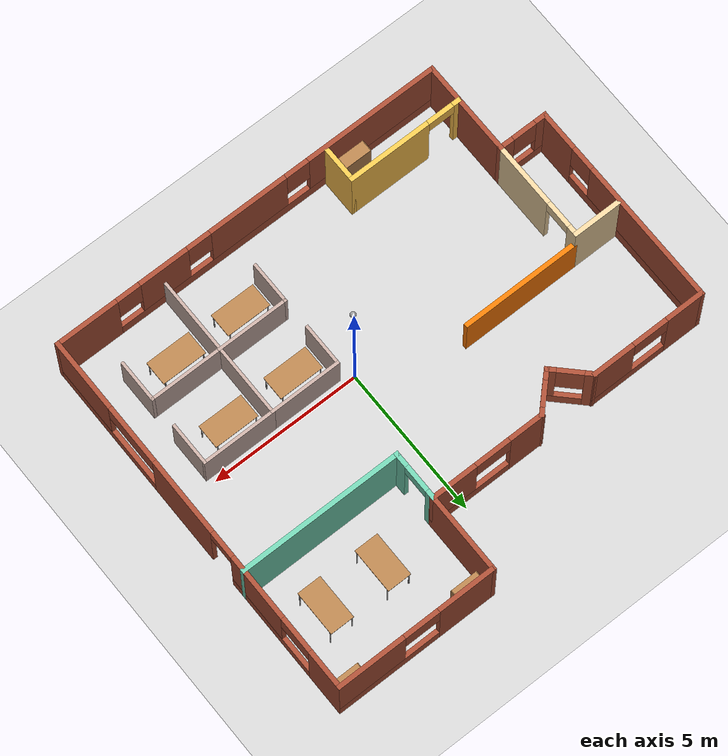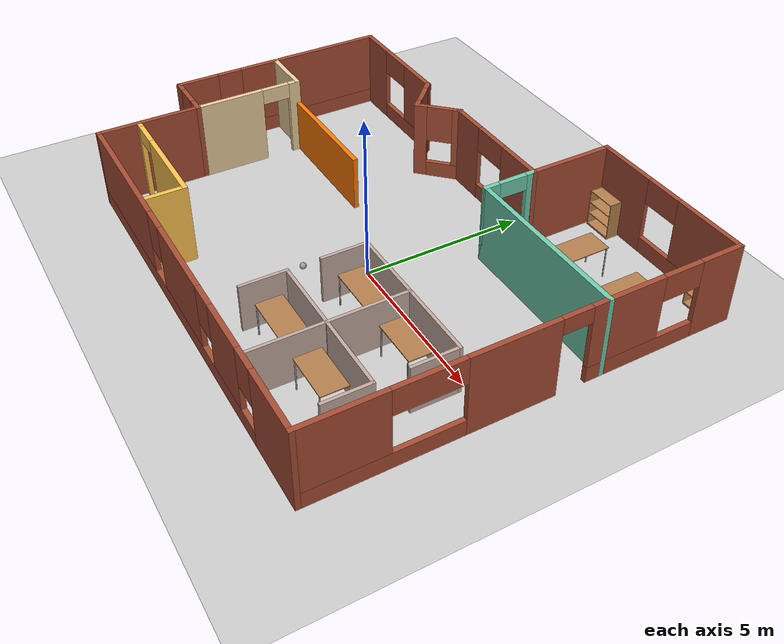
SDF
<sdf version="1.6">
 <world name="default">
  <plugin name="helloworld" filename="libhello.so"/>
  <light name="sun" type="directional">
   <pose>0 0 10 0 -0 0</pose>
   <diffuse>0.8 0.8 0.8 1</diffuse>
   <specular>0.2 0.2 0.2 1</specular>
   <attenuation>
    <range>1000</range>
    <constant>0.9</constant>
    <linear>0.01</linear>
    <quadratic>0.001</quadratic>
   </attenuation>
   <direction>-0.5 0.1 -0.9</direction>
  </light>
  <model name="ground_plane">
   <static>1</static>
   <link name="link">
    <collision name="collision">
     <geometry><plane><normal>0 0 1</normal><size>100 100</size></plane></geometry>
     <surface><friction><ode><mu>100</mu><mu2>50</mu2></ode></friction></surface>
    </collision>
    <visual name="visual">
     <cast_shadows>0</cast_shadows>
     <geometry><plane><normal>0 0 1</normal><size>100 100</size></plane></geometry>
     <material>
      <script><uri>file://media/materials/scripts/gazebo.material</uri><name>Gazebo/Grey</name></script>
     </material>
    </visual>
   </link>
  </model>
  <gravity>0 0 -9.8</gravity>
  <magnetic_field>6e-06 2.3e-05 -4.2e-05</magnetic_field>
  <atmosphere type="adiabatic"/>
  <physics name="default_physics" default="0" type="ode">
   <max_step_size>0.001</max_step_size>
   <real_time_factor>1</real_time_factor>
   <real_time_update_rate>1000</real_time_update_rate>
  </physics>
  <scene><ambient>0.4 0.4 0.4 1</ambient><background>0.7 0.7 0.7 1</background><shadows>1</shadows></scene>
  <spherical_coordinates>
   <surface_model>EARTH_WGS84</surface_model>
   <latitude_deg>0</latitude_deg>
   <longitude_deg>0</longitude_deg>
   <elevation>0</elevation>
   <heading_deg>0</heading_deg>
  </spherical_coordinates>
  <model name="MyOfficeWorld">
   <pose>-1.09735 1.08179 0 0 -0 0</pose>
   <link name="Wall_33">
    <pose>-7.47671 0.275 0 0 -0 1.5708</pose>
    <visual name="Wall_33_Visual_0">
     <pose>-2.83689 0 1.25 0 -0 0</pose>
     <geometry><box><size>1.32622 0.15 2.5</size></box></geometry>
     <material>
      <script><uri>file://media/materials/scripts/gazebo.material</uri><name>Gazebo/Bricks</name></script>
      <ambient>1 1 1 1</ambient>
     </material>
     <meta><layer>0</layer></meta>
    </visual>
    <collision name="Wall_33_Collision_0">
     <geometry><box><size>1.32622 0.15 2.5</size></box></geometry>
     <pose>-2.83689 0 1.25 0 -0 0</pose>
    </collision>
    <visual name="Wall_33_Visual_1">
     <pose>0.66311 0 0.25 0 -0 0</pose>
     <geometry><box><size>5.67378 0.15 0.5</size></box></geometry>
     <material>
      <script><uri>file://media/materials/scripts/gazebo.material</uri><name>Gazebo/Bricks</name></script>
      <ambient>1 1 1 1</ambient>
     </material>
     <meta><layer>0</layer></meta>
    </visual>
    <collision name="Wall_33_Collision_1">
     <geometry><box><size>5.67378 0.15 0.5</size></box></geometry>
     <pose>0.66311 0 0.25 0 -0 0</pose>
    </collision>
    <visual name="Wall_33_Visual_2">
     <pose>1.06311 0 1.5 0 -0 0</pose>
     <geometry><box><size>4.87378 0.15 2</size></box></geometry>
     <material>
      <script><uri>file://media/materials/scripts/gazebo.material</uri><name>Gazebo/Bricks</name></script>
      <ambient>1 1 1 1</ambient>
     </material>
     <meta><layer>0</layer></meta>
    </visual>
    <collision name="Wall_33_Collision_2">
     <geometry><box><size>4.87378 0.15 2</size></box></geometry>
     <pose>1.06311 0 1.5 0 -0 0</pose>
    </collision>
    <visual name="Wall_33_Visual_3">
     <pose>-1.77378 0 1.9 0 -0 0</pose>
     <geometry><box><size>0.8 0.15 1.2</size></box></geometry>
     <material>
      <script><uri>file://media/materials/scripts/gazebo.material</uri><name>Gazebo/Bricks</name></script>
      <ambient>1 1 1 1</ambient>
     </material>
     <meta><layer>0</layer></meta>
    </visual>
    <collision name="Wall_33_Collision_3">
     <geometry><box><size>0.8 0.15 1.2</size></box></geometry>
     <pose>-1.77378 0 1.9 0 -0 0</pose>
    </collision>
   </link>
   <link name="Wall_34">
    <pose>-5.55171 3.7 0 0 -0 0</pose>
    <visual name="Wall_34_Visual_0">
     <pose>-1.33005 0 1.25 0 -0 0</pose>
     <geometry><box><size>1.3399 0.15 2.5</size></box></geometry>
     <material>
      <script><uri>file://media/materials/scripts/gazebo.material</uri><name>Gazebo/Bricks</name></script>
      <ambient>1 1 1 1</ambient>
     </material>
     <meta><layer>0</layer></meta>
    </visual>
    <collision name="Wall_34_Collision_0">
     <geometry><box><size>1.3399 0.15 2.5</size></box></geometry>
     <pose>-1.33005 0 1.25 0 -0 0</pose>
    </collision>
    <visual name="Wall_34_Visual_1">
     <pose>0.66995 0 0.25 0 -0 0</pose>
     <geometry><box><size>2.6601 0.15 0.5</size></box></geometry>
     <material>
      <script><uri>file://media/materials/scripts/gazebo.material</uri><name>Gazebo/Bricks</name></script>
      <ambient>1 1 1 1</ambient>
     </material>
     <meta><layer>0</layer></meta>
    </visual>
    <collision name="Wall_34_Collision_1">
     <geometry><box><size>2.6601 0.15 0.5</size></box></geometry>
     <pose>0.66995 0 0.25 0 -0 0</pose>
    </collision>
    <visual name="Wall_34_Visual_2">
     <pose>1.26995 0 1.5 0 -0 0</pose>
     <geometry><box><size>1.4601 0.15 2</size></box></geometry>
     <material>
      <script><uri>file://media/materials/scripts/gazebo.material</uri><name>Gazebo/Bricks</name></script>
      <ambient>1 1 1 1</ambient>
     </material>
     <meta><layer>0</layer></meta>
    </visual>
    <collision name="Wall_34_Collision_2">
     <geometry><box><size>1.4601 0.15 2</size></box></geometry>
     <pose>1.26995 0 1.5 0 -0 0</pose>
    </collision>
    <visual name="Wall_34_Visual_3">
     <pose>-0.0601 0 2.1 0 -0 0</pose>
     <geometry><box><size>1.2 0.15 0.8</size></box></geometry>
     <material>
      <script><uri>file://media/materials/scripts/gazebo.material</uri><name>Gazebo/Bricks</name></script>
      <ambient>1 1 1 1</ambient>
     </material>
     <meta><layer>0</layer></meta>
    </visual>
    <collision name="Wall_34_Collision_3">
     <geometry><box><size>1.2 0.15 0.8</size></box></geometry>
     <pose>-0.0601 0 2.1 0 -0 0</pose>
    </collision>
   </link>
   <link name="Wall_35">
    <pose>-3.14942 3.2227 0 0 0 -0.785398</pose>
    <visual name="Wall_35_Visual_0">
     <pose>-0.571464 0 1.25 0 -0 0</pose>
     <geometry><box><size>0.357073 0.15 2.5</size></box></geometry>
     <material>
      <script><uri>file://media/materials/scripts/gazebo.material</uri><name>Gazebo/Bricks</name></script>
      <ambient>1 1 1 1</ambient>
     </material>
     <meta><layer>0</layer></meta>
    </visual>
    <collision name="Wall_35_Collision_0">
     <geometry><box><size>0.357073 0.15 2.5</size></box></geometry>
     <pose>-0.571464 0 1.25 0 -0 0</pose>
    </collision>
    <visual name="Wall_35_Visual_1">
     <pose>0.178536 0 0.25 0 -0 0</pose>
     <geometry><box><size>1.14293 0.15 0.5</size></box></geometry>
     <material>
      <script><uri>file://media/materials/scripts/gazebo.material</uri><name>Gazebo/Bricks</name></script>
      <ambient>1 1 1 1</ambient>
     </material>
     <meta><layer>0</layer></meta>
    </visual>
    <collision name="Wall_35_Collision_1">
     <geometry><box><size>1.14293 0.15 0.5</size></box></geometry>
     <pose>0.178536 0 0.25 0 -0 0</pose>
    </collision>
    <visual name="Wall_35_Visual_2">
     <pose>0.578536 0 1.5 0 -0 0</pose>
     <geometry><box><size>0.342927 0.15 2</size></box></geometry>
     <material>
      <script><uri>file://media/materials/scripts/gazebo.material</uri><name>Gazebo/Bricks</name></script>
      <ambient>1 1 1 1</ambient>
     </material>
     <meta><layer>0</layer></meta>
    </visual>
    <collision name="Wall_35_Collision_2">
     <geometry><box><size>0.342927 0.15 2</size></box></geometry>
     <pose>0.578536 0 1.5 0 -0 0</pose>
    </collision>
    <visual name="Wall_35_Visual_3">
     <pose>0.007073 0 1.9 0 -0 0</pose>
     <geometry><box><size>0.8 0.15 1.2</size></box></geometry>
     <material>
      <script><uri>file://media/materials/scripts/gazebo.material</uri><name>Gazebo/Bricks</name></script>
      <ambient>1 1 1 1</ambient>
     </material>
     <meta><layer>0</layer></meta>
    </visual>
    <collision name="Wall_35_Collision_3">
     <geometry><box><size>0.8 0.15 1.2</size></box></geometry>
     <pose>0.007073 0 1.9 0 -0 0</pose>
    </collision>
   </link>
   <link name="Wall_36">
    <pose>-2.19482 3.2227 0 0 -0 0.785398</pose>
    <visual name="Wall_36_Visual_0">
     <pose>-0.549085 0 1.25 0 -0 0</pose>
     <geometry><box><size>0.40183 0.15 2.5</size></box></geometry>
     <material>
      <script><uri>file://media/materials/scripts/gazebo.material</uri><name>Gazebo/Bricks</name></script>
      <ambient>1 1 1 1</ambient>
     </material>
     <meta><layer>0</layer></meta>
    </visual>
    <collision name="Wall_36_Collision_0">
     <geometry><box><size>0.40183 0.15 2.5</size></box></geometry>
     <pose>-0.549085 0 1.25 0 -0 0</pose>
    </collision>
    <visual name="Wall_36_Visual_1">
     <pose>0.200915 0 0.25 0 -0 0</pose>
     <geometry><box><size>1.09817 0.15 0.5</size></box></geometry>
     <material>
      <script><uri>file://media/materials/scripts/gazebo.material</uri><name>Gazebo/Bricks</name></script>
      <ambient>1 1 1 1</ambient>
     </material>
     <meta><layer>0</layer></meta>
    </visual>
    <collision name="Wall_36_Collision_1">
     <geometry><box><size>1.09817 0.15 0.5</size></box></geometry>
     <pose>0.200915 0 0.25 0 -0 0</pose>
    </collision>
    <visual name="Wall_36_Visual_2">
     <pose>0.600915 0 1.5 0 -0 0</pose>
     <geometry><box><size>0.29817 0.15 2</size></box></geometry>
     <material>
      <script><uri>file://media/materials/scripts/gazebo.material</uri><name>Gazebo/Bricks</name></script>
      <ambient>1 1 1 1</ambient>
     </material>
     <meta><layer>0</layer></meta>
    </visual>
    <collision name="Wall_36_Collision_2">
     <geometry><box><size>0.29817 0.15 2</size></box></geometry>
     <pose>0.600915 0 1.5 0 -0 0</pose>
    </collision>
    <visual name="Wall_36_Visual_3">
     <pose>0.05183 0 1.9 0 -0 0</pose>
     <geometry><box><size>0.8 0.15 1.2</size></box></geometry>
     <material>
      <script><uri>file://media/materials/scripts/gazebo.material</uri><name>Gazebo/Bricks</name></script>
      <ambient>1 1 1 1</ambient>
     </material>
     <meta><layer>0</layer></meta>
    </visual>
    <collision name="Wall_36_Collision_3">
     <geometry><box><size>0.8 0.15 1.2</size></box></geometry>
     <pose>0.05183 0 1.9 0 -0 0</pose>
    </collision>
   </link>
   <link name="Wall_37">
    <pose>0.207475 3.7 0 0 -0 0</pose>
    <visual name="Wall_37_Visual_0">
     <pose>-1.38521 0 1.25 0 -0 0</pose>
     <geometry><box><size>1.22958 0.15 2.5</size></box></geometry>
     <material>
      <script><uri>file://media/materials/scripts/gazebo.material</uri><name>Gazebo/Bricks</name></script>
      <ambient>1 1 1 1</ambient>
     </material>
     <meta><layer>0</layer></meta>
    </visual>
    <collision name="Wall_37_Collision_0">
     <geometry><box><size>1.22958 0.15 2.5</size></box></geometry>
     <pose>-1.38521 0 1.25 0 -0 0</pose>
    </collision>
    <visual name="Wall_37_Visual_1">
     <pose>0.614787 0 0.25 0 -0 0</pose>
     <geometry><box><size>2.77042 0.15 0.5</size></box></geometry>
     <material>
      <script><uri>file://media/materials/scripts/gazebo.material</uri><name>Gazebo/Bricks</name></script>
      <ambient>1 1 1 1</ambient>
     </material>
     <meta><layer>0</layer></meta>
    </visual>
    <collision name="Wall_37_Collision_1">
     <geometry><box><size>2.77042 0.15 0.5</size></box></geometry>
     <pose>0.614787 0 0.25 0 -0 0</pose>
    </collision>
    <visual name="Wall_37_Visual_2">
     <pose>1.21479 0 1.5 0 -0 0</pose>
     <geometry><box><size>1.57042 0.15 2</size></box></geometry>
     <material>
      <script><uri>file://media/materials/scripts/gazebo.material</uri><name>Gazebo/Bricks</name></script>
      <ambient>1 1 1 1</ambient>
     </material>
     <meta><layer>0</layer></meta>
    </visual>
    <collision name="Wall_37_Collision_2">
     <geometry><box><size>1.57042 0.15 2</size></box></geometry>
     <pose>1.21479 0 1.5 0 -0 0</pose>
    </collision>
    <visual name="Wall_37_Visual_3">
     <pose>-0.170425 0 2.1 0 -0 0</pose>
     <geometry><box><size>1.2 0.15 0.8</size></box></geometry>
     <material>
      <script><uri>file://media/materials/scripts/gazebo.material</uri><name>Gazebo/Bricks</name></script>
      <ambient>1 1 1 1</ambient>
     </material>
     <meta><layer>0</layer></meta>
    </visual>
    <collision name="Wall_37_Collision_3">
     <geometry><box><size>1.2 0.15 0.8</size></box></geometry>
     <pose>-0.170425 0 2.1 0 -0 0</pose>
    </collision>
   </link>
   <link name="Wall_38">
    <collision name="Wall_38_Collision">
     <geometry><box><size>2.75 0.15 2.5</size></box></geometry>
     <pose>0 0 1.25 0 -0 0</pose>
    </collision>
    <visual name="Wall_38_Visual">
     <pose>0 0 1.25 0 -0 0</pose>
     <geometry><box><size>2.75 0.15 2.5</size></box></geometry>
     <material>
      <script><uri>file://media/materials/scripts/gazebo.material</uri><name>Gazebo/Bricks</name></script>
      <ambient>1 1 1 1</ambient>
     </material>
     <meta><layer>0</layer></meta>
    </visual>
    <pose>2.13247 5 0 0 -0 1.5708</pose>
   </link>
   <link name="Wall_39">
    <pose>4.80748 6.3 0 0 -0 0</pose>
    <visual name="Wall_39_Visual_0">
     <pose>-1.75799 0 1.25 0 -0 0</pose>
     <geometry><box><size>1.98402 0.15 2.5</size></box></geometry>
     <material>
      <script><uri>file://media/materials/scripts/gazebo.material</uri><name>Gazebo/Bricks</name></script>
      <ambient>1 1 1 1</ambient>
     </material>
     <meta><layer>0</layer></meta>
    </visual>
    <collision name="Wall_39_Collision_0">
     <geometry><box><size>1.98402 0.15 2.5</size></box></geometry>
     <pose>-1.75799 0 1.25 0 -0 0</pose>
    </collision>
    <visual name="Wall_39_Visual_1">
     <pose>0.992008 0 0.25 0 -0 0</pose>
     <geometry><box><size>3.51598 0.15 0.5</size></box></geometry>
     <material>
      <script><uri>file://media/materials/scripts/gazebo.material</uri><name>Gazebo/Bricks</name></script>
      <ambient>1 1 1 1</ambient>
     </material>
     <meta><layer>0</layer></meta>
    </visual>
    <collision name="Wall_39_Collision_1">
     <geometry><box><size>3.51598 0.15 0.5</size></box></geometry>
     <pose>0.992008 0 0.25 0 -0 0</pose>
    </collision>
    <visual name="Wall_39_Visual_2">
     <pose>1.59201 0 1.5 0 -0 0</pose>
     <geometry><box><size>2.31598 0.15 2</size></box></geometry>
     <material>
      <script><uri>file://media/materials/scripts/gazebo.material</uri><name>Gazebo/Bricks</name></script>
      <ambient>1 1 1 1</ambient>
     </material>
     <meta><layer>0</layer></meta>
    </visual>
    <collision name="Wall_39_Collision_2">
     <geometry><box><size>2.31598 0.15 2</size></box></geometry>
     <pose>1.59201 0 1.5 0 -0 0</pose>
    </collision>
    <visual name="Wall_39_Visual_3">
     <pose>-0.165984 0 2.1 0 -0 0</pose>
     <geometry><box><size>1.2 0.15 0.8</size></box></geometry>
     <material>
      <script><uri>file://media/materials/scripts/gazebo.material</uri><name>Gazebo/Bricks</name></script>
      <ambient>1 1 1 1</ambient>
     </material>
     <meta><layer>0</layer></meta>
    </visual>
    <collision name="Wall_39_Collision_3">
     <geometry><box><size>1.2 0.15 0.8</size></box></geometry>
     <pose>-0.165984 0 2.1 0 -0 0</pose>
    </collision>
   </link>
   <link name="Wall_45">
    <pose>2.13247 2.9 0 0 0 -1.5708</pose>
    <visual name="Wall_45_Visual_0">
     <pose>-0.705222 0 1.25 0 -0 0</pose>
     <geometry><box><size>0.339556 0.15 2.5</size></box></geometry>
     <material>
      <script><uri>file://media/materials/scripts/gazebo.material</uri><name>Gazebo/Grey</name></script>
      <ambient>0.435294 0.796078 0.67451 1</ambient>
     </material>
     <meta><layer>0</layer></meta>
    </visual>
    <collision name="Wall_45_Collision_0">
     <geometry><box><size>0.339556 0.15 2.5</size></box></geometry>
     <pose>-0.705222 0 1.25 0 -0 0</pose>
    </collision>
    <visual name="Wall_45_Visual_1">
     <pose>0.619778 0 1.25 0 -0 0</pose>
     <geometry><box><size>0.510444 0.15 2.5</size></box></geometry>
     <material>
      <script><uri>file://media/materials/scripts/gazebo.material</uri><name>Gazebo/Grey</name></script>
      <ambient>0.435294 0.796078 0.67451 1</ambient>
     </material>
     <meta><layer>0</layer></meta>
    </visual>
    <collision name="Wall_45_Collision_1">
     <geometry><box><size>0.510444 0.15 2.5</size></box></geometry>
     <pose>0.619778 0 1.25 0 -0 0</pose>
    </collision>
    <visual name="Wall_45_Visual_2">
     <pose>-0.085444 0 2.25 0 -0 0</pose>
     <geometry><box><size>0.9 0.15 0.5</size></box></geometry>
     <material>
      <script><uri>file://media/materials/scripts/gazebo.material</uri><name>Gazebo/Grey</name></script>
      <ambient>0.435294 0.796078 0.67451 1</ambient>
     </material>
     <meta><layer>0</layer></meta>
    </visual>
    <collision name="Wall_45_Collision_2">
     <geometry><box><size>0.9 0.15 0.5</size></box></geometry>
     <pose>-0.085444 0 2.25 0 -0 0</pose>
    </collision>
   </link>
   <link name="Wall_47">
    <collision name="Wall_47_Collision">
     <geometry><box><size>5.5 0.15 2.5</size></box></geometry>
     <pose>0 0 1.25 0 -0 0</pose>
    </collision>
    <visual name="Wall_47_Visual">
     <pose>0 0 1.25 0 -0 0</pose>
     <geometry><box><size>5.5 0.15 2.5</size></box></geometry>
     <material>
      <script><uri>file://media/materials/scripts/gazebo.material</uri><name>Gazebo/Grey</name></script>
      <ambient>0.435294 0.796078 0.67451 1</ambient>
     </material>
     <meta><layer>0</layer></meta>
    </visual>
    <pose>4.80748 2.1 0 0 -0 0</pose>
   </link>
   <link name="Wall_54">
    <pose>7.48247 0 0 0 0 -1.5708</pose>
    <visual name="Wall_54_Visual_0">
     <pose>-5.69597 0 1.25 0 -0 0</pose>
     <geometry><box><size>1.35805 0.15 2.5</size></box></geometry>
     <material>
      <script><uri>file://media/materials/scripts/gazebo.material</uri><name>Gazebo/Bricks</name></script>
      <ambient>1 1 1 1</ambient>
     </material>
     <meta><layer>0</layer></meta>
    </visual>
    <collision name="Wall_54_Collision_0">
     <geometry><box><size>1.35805 0.15 2.5</size></box></geometry>
     <pose>-5.69597 0 1.25 0 -0 0</pose>
    </collision>
    <visual name="Wall_54_Visual_1">
     <pose>0.610952 0 1.25 0 -0 0</pose>
     <geometry><box><size>2.60875 0.15 2.5</size></box></geometry>
     <material>
      <script><uri>file://media/materials/scripts/gazebo.material</uri><name>Gazebo/Bricks</name></script>
      <ambient>1 1 1 1</ambient>
     </material>
     <meta><layer>0</layer></meta>
    </visual>
    <collision name="Wall_54_Collision_1">
     <geometry><box><size>2.60875 0.15 2.5</size></box></geometry>
     <pose>0.610952 0 1.25 0 -0 0</pose>
    </collision>
    <visual name="Wall_54_Visual_2">
     <pose>-3.30519 0 0.25 0 -0 0</pose>
     <geometry><box><size>3.42353 0.15 0.5</size></box></geometry>
     <material>
      <script><uri>file://media/materials/scripts/gazebo.material</uri><name>Gazebo/Bricks</name></script>
      <ambient>1 1 1 1</ambient>
     </material>
     <meta><layer>0</layer></meta>
    </visual>
    <collision name="Wall_54_Collision_2">
     <geometry><box><size>3.42353 0.15 0.5</size></box></geometry>
     <pose>-3.30519 0 0.25 0 -0 0</pose>
    </collision>
    <visual name="Wall_54_Visual_3">
     <pose>4.14516 0 0.25 0 -0 0</pose>
     <geometry><box><size>4.45967 0.15 0.5</size></box></geometry>
     <material>
      <script><uri>file://media/materials/scripts/gazebo.material</uri><name>Gazebo/Bricks</name></script>
      <ambient>1 1 1 1</ambient>
     </material>
     <meta><layer>0</layer></meta>
    </visual>
    <collision name="Wall_54_Collision_3">
     <geometry><box><size>4.45967 0.15 0.5</size></box></geometry>
     <pose>4.14516 0 0.25 0 -0 0</pose>
    </collision>
    <visual name="Wall_54_Visual_4">
     <pose>-2.70519 0 1.5 0 -0 0</pose>
     <geometry><box><size>2.22352 0.15 2</size></box></geometry>
     <material>
      <script><uri>file://media/materials/scripts/gazebo.material</uri><name>Gazebo/Bricks</name></script>
      <ambient>1 1 1 1</ambient>
     </material>
     <meta><layer>0</layer></meta>
    </visual>
    <collision name="Wall_54_Collision_4">
     <geometry><box><size>2.22352 0.15 2</size></box></geometry>
     <pose>-2.70519 0 1.5 0 -0 0</pose>
    </collision>
    <visual name="Wall_54_Visual_5">
     <pose>-2.70519 0 1.5 0 -0 0</pose>
     <geometry><box><size>2.22352 0.15 2</size></box></geometry>
     <material>
      <script><uri>file://media/materials/scripts/gazebo.material</uri><name>Gazebo/Bricks</name></script>
      <ambient>1 1 1 1</ambient>
     </material>
     <meta><layer>0</layer></meta>
    </visual>
    <collision name="Wall_54_Collision_5">
     <geometry><box><size>2.22352 0.15 2</size></box></geometry>
     <pose>-2.70519 0 1.5 0 -0 0</pose>
    </collision>
    <visual name="Wall_54_Visual_6">
     <pose>5.14516 0 1.5 0 -0 0</pose>
     <geometry><box><size>2.45967 0.15 2</size></box></geometry>
     <material>
      <script><uri>file://media/materials/scripts/gazebo.material</uri><name>Gazebo/Bricks</name></script>
      <ambient>1 1 1 1</ambient>
     </material>
     <meta><layer>0</layer></meta>
    </visual>
    <collision name="Wall_54_Collision_6">
     <geometry><box><size>2.45967 0.15 2</size></box></geometry>
     <pose>5.14516 0 1.5 0 -0 0</pose>
    </collision>
    <visual name="Wall_54_Visual_7">
     <pose>-4.41695 0 2.1 0 -0 0</pose>
     <geometry><box><size>1.2 0.15 0.8</size></box></geometry>
     <material>
      <script><uri>file://media/materials/scripts/gazebo.material</uri><name>Gazebo/Bricks</name></script>
      <ambient>1 1 1 1</ambient>
     </material>
     <meta><layer>0</layer></meta>
    </visual>
    <collision name="Wall_54_Collision_7">
     <geometry><box><size>1.2 0.15 0.8</size></box></geometry>
     <pose>-4.41695 0 2.1 0 -0 0</pose>
    </collision>
    <visual name="Wall_54_Visual_8">
     <pose>2.91533 0 2.1 0 -0 0</pose>
     <geometry><box><size>2 0.15 0.8</size></box></geometry>
     <material>
      <script><uri>file://media/materials/scripts/gazebo.material</uri><name>Gazebo/Bricks</name></script>
      <ambient>1 1 1 1</ambient>
     </material>
     <meta><layer>0</layer></meta>
    </visual>
    <collision name="Wall_54_Collision_8">
     <geometry><box><size>2 0.15 0.8</size></box></geometry>
     <pose>2.91533 0 2.1 0 -0 0</pose>
    </collision>
    <visual name="Wall_54_Visual_9">
     <pose>-1.14342 0 2.25 0 -0 0</pose>
     <geometry><box><size>0.9 0.15 0.5</size></box></geometry>
     <material>
      <script><uri>file://media/materials/scripts/gazebo.material</uri><name>Gazebo/Bricks</name></script>
      <ambient>1 1 1 1</ambient>
     </material>
     <meta><layer>0</layer></meta>
    </visual>
    <collision name="Wall_54_Collision_9">
     <geometry><box><size>0.9 0.15 0.5</size></box></geometry>
     <pose>-1.14342 0 2.25 0 -0 0</pose>
    </collision>
    <visual name="Wall_54_Visual_10">
     <pose>-1.14342 0 2.25 0 -0 0</pose>
     <geometry><box><size>0.9 0.15 0.5</size></box></geometry>
     <material>
      <script><uri>file://media/materials/scripts/gazebo.material</uri><name>Gazebo/Bricks</name></script>
      <ambient>1 1 1 1</ambient>
     </material>
     <meta><layer>0</layer></meta>
    </visual>
    <collision name="Wall_54_Collision_10">
     <geometry><box><size>0.9 0.15 0.5</size></box></geometry>
     <pose>-1.14342 0 2.25 0 -0 0</pose>
    </collision>
   </link>
   <link name="Wall_55">
    <pose>0.807475 -6.3 0 0 -0 3.14159</pose>
    <visual name="Wall_55_Visual_0">
     <pose>-5.68732 0 1.25 0 -0 0</pose>
     <geometry><box><size>2.12537 0.15 2.5</size></box></geometry>
     <material>
      <script><uri>file://media/materials/scripts/gazebo.material</uri><name>Gazebo/Bricks</name></script>
      <ambient>1 1 1 1</ambient>
     </material>
     <meta><layer>0</layer></meta>
    </visual>
    <collision name="Wall_55_Collision_0">
     <geometry><box><size>2.12537 0.15 2.5</size></box></geometry>
     <pose>-5.68732 0 1.25 0 -0 0</pose>
    </collision>
    <visual name="Wall_55_Visual_1">
     <pose>1.06268 0 0.25 0 -0 0</pose>
     <geometry><box><size>11.3746 0.15 0.5</size></box></geometry>
     <material>
      <script><uri>file://media/materials/scripts/gazebo.material</uri><name>Gazebo/Bricks</name></script>
      <ambient>1 1 1 1</ambient>
     </material>
     <meta><layer>0</layer></meta>
    </visual>
    <collision name="Wall_55_Collision_1">
     <geometry><box><size>11.3746 0.15 0.5</size></box></geometry>
     <pose>1.06268 0 0.25 0 -0 0</pose>
    </collision>
    <visual name="Wall_55_Visual_2">
     <pose>-2.98241 0 1.5 0 -0 0</pose>
     <geometry><box><size>1.68445 0.15 2</size></box></geometry>
     <material>
      <script><uri>file://media/materials/scripts/gazebo.material</uri><name>Gazebo/Bricks</name></script>
      <ambient>1 1 1 1</ambient>
     </material>
     <meta><layer>0</layer></meta>
    </visual>
    <collision name="Wall_55_Collision_2">
     <geometry><box><size>1.68445 0.15 2</size></box></geometry>
     <pose>-2.98241 0 1.5 0 -0 0</pose>
    </collision>
    <visual name="Wall_55_Visual_3">
     <pose>0.012013 0 1.5 0 -0 0</pose>
     <geometry><box><size>2.70439 0.15 2</size></box></geometry>
     <material>
      <script><uri>file://media/materials/scripts/gazebo.material</uri><name>Gazebo/Bricks</name></script>
      <ambient>1 1 1 1</ambient>
     </material>
     <meta><layer>0</layer></meta>
    </visual>
    <collision name="Wall_55_Collision_3">
     <geometry><box><size>2.70439 0.15 2</size></box></geometry>
     <pose>0.012013 0 1.5 0 -0 0</pose>
    </collision>
    <visual name="Wall_55_Visual_4">
     <pose>4.4571 0 1.5 0 -0 0</pose>
     <geometry><box><size>4.58579 0.15 2</size></box></geometry>
     <material>
      <script><uri>file://media/materials/scripts/gazebo.material</uri><name>Gazebo/Bricks</name></script>
      <ambient>1 1 1 1</ambient>
     </material>
     <meta><layer>0</layer></meta>
    </visual>
    <collision name="Wall_55_Collision_4">
     <geometry><box><size>4.58579 0.15 2</size></box></geometry>
     <pose>4.4571 0 1.5 0 -0 0</pose>
    </collision>
    <visual name="Wall_55_Visual_5">
     <pose>-4.22463 0 1.9 0 -0 0</pose>
     <geometry><box><size>0.8 0.15 1.2</size></box></geometry>
     <material>
      <script><uri>file://media/materials/scripts/gazebo.material</uri><name>Gazebo/Bricks</name></script>
      <ambient>1 1 1 1</ambient>
     </material>
     <meta><layer>0</layer></meta>
    </visual>
    <collision name="Wall_55_Collision_5">
     <geometry><box><size>0.8 0.15 1.2</size></box></geometry>
     <pose>-4.22463 0 1.9 0 -0 0</pose>
    </collision>
    <visual name="Wall_55_Visual_6">
     <pose>-1.74018 0 1.9 0 -0 0</pose>
     <geometry><box><size>0.8 0.15 1.2</size></box></geometry>
     <material>
      <script><uri>file://media/materials/scripts/gazebo.material</uri><name>Gazebo/Bricks</name></script>
      <ambient>1 1 1 1</ambient>
     </material>
     <meta><layer>0</layer></meta>
    </visual>
    <collision name="Wall_55_Collision_6">
     <geometry><box><size>0.8 0.15 1.2</size></box></geometry>
     <pose>-1.74018 0 1.9 0 -0 0</pose>
    </collision>
    <visual name="Wall_55_Visual_7">
     <pose>1.76421 0 1.9 0 -0 0</pose>
     <geometry><box><size>0.8 0.15 1.2</size></box></geometry>
     <material>
      <script><uri>file://media/materials/scripts/gazebo.material</uri><name>Gazebo/Bricks</name></script>
      <ambient>1 1 1 1</ambient>
     </material>
     <meta><layer>0</layer></meta>
    </visual>
    <collision name="Wall_55_Collision_7">
     <geometry><box><size>0.8 0.15 1.2</size></box></geometry>
     <pose>1.76421 0 1.9 0 -0 0</pose>
    </collision>
   </link>
   <link name="Wall_56">
    <collision name="Wall_56_Collision">
     <geometry><box><size>3.25 0.15 2.5</size></box></geometry>
     <pose>0 0 1.25 0 -0 0</pose>
    </collision>
    <visual name="Wall_56_Visual">
     <pose>0 0 1.25 0 -0 0</pose>
     <geometry><box><size>3.25 0.15 2.5</size></box></geometry>
     <material>
      <script><uri>file://media/materials/scripts/gazebo.material</uri><name>Gazebo/Bricks</name></script>
      <ambient>1 1 1 1</ambient>
     </material>
     <meta><layer>0</layer></meta>
    </visual>
    <pose>-5.86752 -4.75 0 0 -0 1.5708</pose>
   </link>
   <link name="Wall_58">
    <pose>-6.67494 -3.19954 0 0 -0 3.14103</pose>
    <visual name="Wall_58_Visual_0">
     <pose>-0.623586 0 1.25 0 -0 0</pose>
     <geometry><box><size>0.517811 0.15 2.5</size></box></geometry>
     <material>
      <script><uri>file://media/materials/scripts/gazebo.material</uri><name>Gazebo/Bricks</name></script>
      <ambient>1 1 1 1</ambient>
     </material>
     <meta><layer>0</layer></meta>
    </visual>
    <collision name="Wall_58_Collision_0">
     <geometry><box><size>0.517811 0.15 2.5</size></box></geometry>
     <pose>-0.623586 0 1.25 0 -0 0</pose>
    </collision>
    <visual name="Wall_58_Visual_1">
     <pose>0.258905 0 0.25 0 -0 0</pose>
     <geometry><box><size>1.24717 0.15 0.5</size></box></geometry>
     <material>
      <script><uri>file://media/materials/scripts/gazebo.material</uri><name>Gazebo/Bricks</name></script>
      <ambient>1 1 1 1</ambient>
     </material>
     <meta><layer>0</layer></meta>
    </visual>
    <collision name="Wall_58_Collision_1">
     <geometry><box><size>1.24717 0.15 0.5</size></box></geometry>
     <pose>0.258905 0 0.25 0 -0 0</pose>
    </collision>
    <visual name="Wall_58_Visual_2">
     <pose>0.658905 0 1.5 0 -0 0</pose>
     <geometry><box><size>0.447171 0.15 2</size></box></geometry>
     <material>
      <script><uri>file://media/materials/scripts/gazebo.material</uri><name>Gazebo/Bricks</name></script>
      <ambient>1 1 1 1</ambient>
     </material>
     <meta><layer>0</layer></meta>
    </visual>
    <collision name="Wall_58_Collision_2">
     <geometry><box><size>0.447171 0.15 2</size></box></geometry>
     <pose>0.658905 0 1.5 0 -0 0</pose>
    </collision>
    <visual name="Wall_58_Visual_3">
     <pose>0.03532 0 1.9 0 -0 0</pose>
     <geometry><box><size>0.8 0.15 1.2</size></box></geometry>
     <material>
      <script><uri>file://media/materials/scripts/gazebo.material</uri><name>Gazebo/Bricks</name></script>
      <ambient>1 1 1 1</ambient>
     </material>
     <meta><layer>0</layer></meta>
    </visual>
    <collision name="Wall_58_Collision_3">
     <geometry><box><size>0.8 0.15 1.2</size></box></geometry>
     <pose>0.03532 0 1.9 0 -0 0</pose>
    </collision>
   </link>
   <link name="Wall_60">
    <collision name="Wall_60_Collision">
     <geometry><box><size>4.96295 0.1 1.5</size></box></geometry>
     <pose>0 0 0.75 0 -0 0</pose>
    </collision>
    <visual name="Wall_60_Visual">
     <pose>0 0 0.75 0 -0 0</pose>
     <geometry><box><size>4.96295 0.1 1.5</size></box></geometry>
     <material>
      <script><uri>file://media/materials/scripts/gazebo.material</uri><name>Gazebo/Grey</name></script>
      <ambient>0.760784 0.662745 0.627451 1</ambient>
     </material>
     <meta><layer>0</layer></meta>
    </visual>
    <pose>3.85035 -3.73329 0 0 -0 1.5708</pose>
   </link>
   <link name="Wall_76">
    <collision name="Wall_76_Collision">
     <geometry><box><size>2.49733 0.1 1.5</size></box></geometry>
     <pose>0 0 0.75 0 -0 0</pose>
    </collision>
    <visual name="Wall_76_Visual">
     <pose>0 0 0.75 0 -0 0</pose>
     <geometry><box><size>2.49733 0.1 1.5</size></box></geometry>
     <material>
      <script><uri>file://media/materials/scripts/gazebo.material</uri><name>Gazebo/Grey</name></script>
      <ambient>0.760784 0.662745 0.627451 1</ambient>
     </material>
     <meta><layer>0</layer></meta>
    </visual>
    <pose>5.04885 -1.30179 0 0 -0 0</pose>
   </link>
   <link name="Wall_77">
    <collision name="Wall_77_Collision">
     <geometry><box><size>1.46981 0.1 1.5</size></box></geometry>
     <pose>0 0 0.75 0 -0 0</pose>
    </collision>
    <visual name="Wall_77_Visual">
     <pose>0 0 0.75 0 -0 0</pose>
     <geometry><box><size>1.46981 0.1 1.5</size></box></geometry>
     <material>
      <script><uri>file://media/materials/scripts/gazebo.material</uri><name>Gazebo/Grey</name></script>
      <ambient>0.760784 0.662745 0.627451 1</ambient>
     </material>
     <meta><layer>0</layer></meta>
    </visual>
    <pose>6.24735 -1.98679 0 0 0 -1.5708</pose>
   </link>
   <link name="Wall_79">
    <collision name="Wall_79_Collision">
     <geometry><box><size>2.467 0.1 1.5</size></box></geometry>
     <pose>0 0 0.75 0 -0 0</pose>
    </collision>
    <visual name="Wall_79_Visual">
     <pose>0 0 0.75 0 -0 0</pose>
     <geometry><box><size>2.467 0.1 1.5</size></box></geometry>
     <material>
      <script><uri>file://media/materials/scripts/gazebo.material</uri><name>Gazebo/Grey</name></script>
      <ambient>0.760784 0.662745 0.627451 1</ambient>
     </material>
     <meta><layer>0</layer></meta>
    </visual>
    <pose>5.06385 -3.68479 0 0 -0 0</pose>
   </link>
   <link name="Wall_80">
    <collision name="Wall_80_Collision">
     <geometry><box><size>1.45009 0.1 1.5</size></box></geometry>
     <pose>0 0 0.75 0 -0 0</pose>
    </collision>
    <visual name="Wall_80_Visual">
     <pose>0 0 0.75 0 -0 0</pose>
     <geometry><box><size>1.45009 0.1 1.5</size></box></geometry>
     <material>
      <script><uri>file://media/materials/scripts/gazebo.material</uri><name>Gazebo/Grey</name></script>
      <ambient>0.760784 0.662745 0.627451 1</ambient>
     </material>
     <meta><layer>0</layer></meta>
    </visual>
    <pose>6.24735 -4.35979 0 0 0 -1.5708</pose>
   </link>
   <link name="Wall_85">
    <collision name="Wall_85_Collision">
     <geometry><box><size>2.447 0.1 1.5</size></box></geometry>
     <pose>0 0 0.75 0 -0 0</pose>
    </collision>
    <visual name="Wall_85_Visual">
     <pose>0 0 0.75 0 -0 0</pose>
     <geometry><box><size>2.447 0.1 1.5</size></box></geometry>
     <material>
      <script><uri>file://media/materials/scripts/gazebo.material</uri><name>Gazebo/Grey</name></script>
      <ambient>0.760784 0.662745 0.627451 1</ambient>
     </material>
     <meta><layer>0</layer></meta>
    </visual>
    <pose>2.70685 -3.68479 0 0 -0 3.14159</pose>
   </link>
   <link name="Wall_86">
    <collision name="Wall_86_Collision">
     <geometry><box><size>1.45001 0.1 1.5</size></box></geometry>
     <pose>0 0 0.75 0 -0 0</pose>
    </collision>
    <visual name="Wall_86_Visual">
     <pose>0 0 0.75 0 -0 0</pose>
     <geometry><box><size>1.45001 0.1 1.5</size></box></geometry>
     <material>
      <script><uri>file://media/materials/scripts/gazebo.material</uri><name>Gazebo/Grey</name></script>
      <ambient>0.760784 0.662745 0.627451 1</ambient>
     </material>
     <meta><layer>0</layer></meta>
    </visual>
    <pose>1.53335 -4.35979 0 0 0 -1.5708</pose>
   </link>
   <link name="Wall_89">
    <collision name="Wall_89_Collision">
     <geometry><box><size>2.417 0.1 1.5</size></box></geometry>
     <pose>0 0 0.75 0 -0 0</pose>
    </collision>
    <visual name="Wall_89_Visual">
     <pose>0 0 0.75 0 -0 0</pose>
     <geometry><box><size>2.417 0.1 1.5</size></box></geometry>
     <material>
      <script><uri>file://media/materials/scripts/gazebo.material</uri><name>Gazebo/Grey</name></script>
      <ambient>0.760784 0.662745 0.627451 1</ambient>
     </material>
     <meta><layer>0</layer></meta>
    </visual>
    <pose>2.69185 -1.30179 0 0 -0 3.14159</pose>
   </link>
   <link name="Wall_90">
    <collision name="Wall_90_Collision">
     <geometry><box><size>1.46293 0.1 1.5</size></box></geometry>
     <pose>0 0 0.75 0 -0 0</pose>
    </collision>
    <visual name="Wall_90_Visual">
     <pose>0 0 0.75 0 -0 0</pose>
     <geometry><box><size>1.46293 0.1 1.5</size></box></geometry>
     <material>
      <script><uri>file://media/materials/scripts/gazebo.material</uri><name>Gazebo/Grey</name></script>
      <ambient>0.760784 0.662745 0.627451 1</ambient>
     </material>
     <meta><layer>0</layer></meta>
    </visual>
    <pose>1.53335 -1.98329 0 0 0 -1.5708</pose>
   </link>
   <link name="Wall_92">
    <pose>-3.91363 -5.07538 0 0 -0 0</pose>
    <visual name="Wall_92_Visual_0">
     <pose>-1.85624 0 1.25 0 -0 0</pose>
     <geometry><box><size>0.287509 0.15 2.5</size></box></geometry>
     <material>
      <script><uri>file://media/materials/scripts/gazebo.material</uri><name>Gazebo/Grey</name></script>
      <ambient>1 0.764706 0.305882 1</ambient>
     </material>
     <meta><layer>0</layer></meta>
    </visual>
    <collision name="Wall_92_Collision_0">
     <geometry><box><size>0.287509 0.15 2.5</size></box></geometry>
     <pose>-1.85624 0 1.25 0 -0 0</pose>
    </collision>
    <visual name="Wall_92_Visual_1">
     <pose>0.593755 0 1.25 0 -0 0</pose>
     <geometry><box><size>2.81249 0.15 2.5</size></box></geometry>
     <material>
      <script><uri>file://media/materials/scripts/gazebo.material</uri><name>Gazebo/Grey</name></script>
      <ambient>1 0.764706 0.305882 1</ambient>
     </material>
     <meta><layer>0</layer></meta>
    </visual>
    <collision name="Wall_92_Collision_1">
     <geometry><box><size>2.81249 0.15 2.5</size></box></geometry>
     <pose>0.593755 0 1.25 0 -0 0</pose>
    </collision>
    <visual name="Wall_92_Visual_2">
     <pose>-1.26249 0 2.25 0 -0 0</pose>
     <geometry><box><size>0.9 0.15 0.5</size></box></geometry>
     <material>
      <script><uri>file://media/materials/scripts/gazebo.material</uri><name>Gazebo/Grey</name></script>
      <ambient>1 0.764706 0.305882 1</ambient>
     </material>
     <meta><layer>0</layer></meta>
    </visual>
    <collision name="Wall_92_Collision_2">
     <geometry><box><size>0.9 0.15 0.5</size></box></geometry>
     <pose>-1.26249 0 2.25 0 -0 0</pose>
    </collision>
   </link>
   <link name="Wall_93">
    <collision name="Wall_93_Collision">
     <geometry><box><size>1.25 0.15 2.5</size></box></geometry>
     <pose>0 0 1.25 0 -0 0</pose>
    </collision>
    <visual name="Wall_93_Visual">
     <pose>0 0 1.25 0 -0 0</pose>
     <geometry><box><size>1.25 0.15 2.5</size></box></geometry>
     <material>
      <script><uri>file://media/materials/scripts/gazebo.material</uri><name>Gazebo/Grey</name></script>
      <ambient>1 0.764706 0.305882 1</ambient>
     </material>
     <meta><layer>0</layer></meta>
    </visual>
    <pose>-1.98863 -5.62538 0 0 0 -1.5708</pose>
   </link>
   <link name="Wall_95">
    <collision name="Wall_95_Collision">
     <geometry><box><size>4 0.15 1.75</size></box></geometry>
     <pose>0 0 0.875 0 -0 0</pose>
    </collision>
    <visual name="Wall_95_Visual">
     <pose>0 0 0.875 0 -0 0</pose>
     <geometry><box><size>4 0.15 1.75</size></box></geometry>
     <material>
      <script><uri>file://media/materials/scripts/gazebo.material</uri><name>Gazebo/Grey</name></script>
      <ambient>0.996078 0.47451 0.0196078 1</ambient>
     </material>
     <meta><layer>0</layer></meta>
    </visual>
    <pose>-3.88815 0.151625 0 0 -0 0</pose>
   </link>
   <link name="Wall_97">
    <pose>-5.86752 -1.525 0 0 -0 1.5708</pose>
    <visual name="Wall_97_Visual_0">
     <pose>-0.641316 0 1.25 0 -0 0</pose>
     <geometry><box><size>2.21737 0.15 2.5</size></box></geometry>
     <material>
      <script><uri>file://media/materials/scripts/gazebo.material</uri><name>Gazebo/Grey</name></script>
      <ambient>0.921569 0.807843 0.615686 1</ambient>
     </material>
     <meta><layer>0</layer></meta>
    </visual>
    <collision name="Wall_97_Collision_0">
     <geometry><box><size>2.21737 0.15 2.5</size></box></geometry>
     <pose>-0.641316 0 1.25 0 -0 0</pose>
    </collision>
    <visual name="Wall_97_Visual_1">
     <pose>1.55868 0 1.25 0 -0 0</pose>
     <geometry><box><size>0.382633 0.15 2.5</size></box></geometry>
     <material>
      <script><uri>file://media/materials/scripts/gazebo.material</uri><name>Gazebo/Grey</name></script>
      <ambient>0.921569 0.807843 0.615686 1</ambient>
     </material>
     <meta><layer>0</layer></meta>
    </visual>
    <collision name="Wall_97_Collision_1">
     <geometry><box><size>0.382633 0.15 2.5</size></box></geometry>
     <pose>1.55868 0 1.25 0 -0 0</pose>
    </collision>
    <visual name="Wall_97_Visual_2">
     <pose>0.917367 0 2.25 0 -0 0</pose>
     <geometry><box><size>0.9 0.15 0.5</size></box></geometry>
     <material>
      <script><uri>file://media/materials/scripts/gazebo.material</uri><name>Gazebo/Grey</name></script>
      <ambient>0.921569 0.807843 0.615686 1</ambient>
     </material>
     <meta><layer>0</layer></meta>
    </visual>
    <collision name="Wall_97_Collision_2">
     <geometry><box><size>0.9 0.15 0.5</size></box></geometry>
     <pose>0.917367 0 2.25 0 -0 0</pose>
    </collision>
   </link>
   <link name="Wall_99">
    <collision name="Wall_99_Collision">
     <geometry><box><size>1.75 0.15 2.5</size></box></geometry>
     <pose>0 0 1.25 0 -0 0</pose>
    </collision>
    <visual name="Wall_99_Visual">
     <pose>0 0 1.25 0 -0 0</pose>
     <geometry><box><size>1.75 0.15 2.5</size></box></geometry>
     <material>
      <script><uri>file://media/materials/scripts/gazebo.material</uri><name>Gazebo/Grey</name></script>
      <ambient>0.921569 0.807843 0.615686 1</ambient>
     </material>
     <meta><layer>0</layer></meta>
    </visual>
    <pose>-6.66753 0.15 0 0 -0 3.14159</pose>
   </link>
   <static>1</static>
  </model>
  <model name="bookshelf">
   <static>1</static>
   <link name="link">
    <inertial><mass>1</mass></inertial>
    <collision name="back">
     <pose>0 0.005 0.6 0 -0 0</pose>
     <geometry><box><size>0.9 0.01 1.2</size></box></geometry>
    </collision>
    <visual name="visual1">
     <pose>0 0.005 0.6 0 -0 0</pose>
     <geometry><box><size>0.9 0.01 1.2</size></box></geometry>
     <material>
      <script><uri>file://media/materials/scripts/gazebo.material</uri><name>Gazebo/Wood</name></script>
     </material>
    </visual>
    <collision name="left_side">
     <pose>0.45 -0.195 0.6 0 -0 0</pose>
     <geometry><box><size>0.02 0.4 1.2</size></box></geometry>
    </collision>
    <visual name="visual2">
     <pose>0.45 -0.195 0.6 0 -0 0</pose>
     <geometry><box><size>0.02 0.4 1.2</size></box></geometry>
     <material>
      <script><uri>file://media/materials/scripts/gazebo.material</uri><name>Gazebo/Wood</name></script>
     </material>
    </visual>
    <collision name="right_side">
     <pose>-0.45 -0.195 0.6 0 -0 0</pose>
     <geometry><box><size>0.02 0.4 1.2</size></box></geometry>
    </collision>
    <visual name="visual3">
     <pose>-0.45 -0.195 0.6 0 -0 0</pose>
     <geometry><box><size>0.02 0.4 1.2</size></box></geometry>
     <material>
      <script><uri>file://media/materials/scripts/gazebo.material</uri><name>Gazebo/Wood</name></script>
     </material>
    </visual>
    <collision name="bottom">
     <pose>0 -0.195 0.03 0 -0 0</pose>
     <geometry><box><size>0.88 0.4 0.06</size></box></geometry>
    </collision>
    <visual name="visual4">
     <pose>0 -0.195 0.03 0 -0 0</pose>
     <geometry><box><size>0.88 0.4 0.06</size></box></geometry>
     <material>
      <script><uri>file://media/materials/scripts/gazebo.material</uri><name>Gazebo/Wood</name></script>
     </material>
    </visual>
    <collision name="top">
     <pose>0 -0.195 1.19 0 -0 0</pose>
     <geometry><box><size>0.88 0.4 0.02</size></box></geometry>
    </collision>
    <visual name="visual5">
     <pose>0 -0.195 1.19 0 -0 0</pose>
     <geometry><box><size>0.88 0.4 0.02</size></box></geometry>
     <material>
      <script><uri>file://media/materials/scripts/gazebo.material</uri><name>Gazebo/Wood</name></script>
     </material>
    </visual>
    <collision name="low_shelf">
     <pose>0 -0.195 0.43 0 -0 0</pose>
     <geometry><box><size>0.88 0.4 0.02</size></box></geometry>
    </collision>
    <visual name="visual6">
     <pose>0 -0.195 0.43 0 -0 0</pose>
     <geometry><box><size>0.88 0.4 0.02</size></box></geometry>
     <material>
      <script><uri>file://media/materials/scripts/gazebo.material</uri><name>Gazebo/Wood</name></script>
     </material>
    </visual>
    <collision name="high_shelf">
     <pose>0 -0.195 0.8 0 -0 0</pose>
     <geometry><box><size>0.88 0.4 0.02</size></box></geometry>
    </collision>
    <visual name="visual7">
     <pose>0 -0.195 0.8 0 -0 0</pose>
     <geometry><box><size>0.88 0.4 0.02</size></box></geometry>
     <material>
      <script><uri>file://media/materials/scripts/gazebo.material</uri><name>Gazebo/Wood</name></script>
     </material>
    </visual>
   </link>
   <pose>1.62564 7.26877 0 0 -0 0</pose>
  </model>
  <model name="bookshelf_0">
   <static>1</static>
   <link name="link">
    <inertial><mass>1</mass></inertial>
    <collision name="back">
     <pose>0 0.005 0.6 0 -0 0</pose>
     <geometry><box><size>0.9 0.01 1.2</size></box></geometry>
    </collision>
    <visual name="visual1">
     <pose>0 0.005 0.6 0 -0 0</pose>
     <geometry><box><size>0.9 0.01 1.2</size></box></geometry>
     <material>
      <script><uri>file://media/materials/scripts/gazebo.material</uri><name>Gazebo/Wood</name></script>
     </material>
    </visual>
    <collision name="left_side">
     <pose>0.45 -0.195 0.6 0 -0 0</pose>
     <geometry><box><size>0.02 0.4 1.2</size></box></geometry>
    </collision>
    <visual name="visual2">
     <pose>0.45 -0.195 0.6 0 -0 0</pose>
     <geometry><box><size>0.02 0.4 1.2</size></box></geometry>
     <material>
      <script><uri>file://media/materials/scripts/gazebo.material</uri><name>Gazebo/Wood</name></script>
     </material>
    </visual>
    <collision name="right_side">
     <pose>-0.45 -0.195 0.6 0 -0 0</pose>
     <geometry><box><size>0.02 0.4 1.2</size></box></geometry>
    </collision>
    <visual name="visual3">
     <pose>-0.45 -0.195 0.6 0 -0 0</pose>
     <geometry><box><size>0.02 0.4 1.2</size></box></geometry>
     <material>
      <script><uri>file://media/materials/scripts/gazebo.material</uri><name>Gazebo/Wood</name></script>
     </material>
    </visual>
    <collision name="bottom">
     <pose>0 -0.195 0.03 0 -0 0</pose>
     <geometry><box><size>0.88 0.4 0.06</size></box></geometry>
    </collision>
    <visual name="visual4">
     <pose>0 -0.195 0.03 0 -0 0</pose>
     <geometry><box><size>0.88 0.4 0.06</size></box></geometry>
     <material>
      <script><uri>file://media/materials/scripts/gazebo.material</uri><name>Gazebo/Wood</name></script>
     </material>
    </visual>
    <collision name="top">
     <pose>0 -0.195 1.19 0 -0 0</pose>
     <geometry><box><size>0.88 0.4 0.02</size></box></geometry>
    </collision>
    <visual name="visual5">
     <pose>0 -0.195 1.19 0 -0 0</pose>
     <geometry><box><size>0.88 0.4 0.02</size></box></geometry>
     <material>
      <script><uri>file://media/materials/scripts/gazebo.material</uri><name>Gazebo/Wood</name></script>
     </material>
    </visual>
    <collision name="low_shelf">
     <pose>0 -0.195 0.43 0 -0 0</pose>
     <geometry><box><size>0.88 0.4 0.02</size></box></geometry>
    </collision>
    <visual name="visual6">
     <pose>0 -0.195 0.43 0 -0 0</pose>
     <geometry><box><size>0.88 0.4 0.02</size></box></geometry>
     <material>
      <script><uri>file://media/materials/scripts/gazebo.material</uri><name>Gazebo/Wood</name></script>
     </material>
    </visual>
    <collision name="high_shelf">
     <pose>0 -0.195 0.8 0 -0 0</pose>
     <geometry><box><size>0.88 0.4 0.02</size></box></geometry>
    </collision>
    <visual name="visual7">
     <pose>0 -0.195 0.8 0 -0 0</pose>
     <geometry><box><size>0.88 0.4 0.02</size></box></geometry>
     <material>
      <script><uri>file://media/materials/scripts/gazebo.material</uri><name>Gazebo/Wood</name></script>
     </material>
    </visual>
   </link>
   <pose>5.82156 7.26877 0 0 -0 0</pose>
  </model>
  <model name="bookshelf_1">
   <static>1</static>
   <link name="link">
    <inertial><mass>1</mass></inertial>
    <collision name="back">
     <pose>0 0.005 0.6 0 -0 0</pose>
     <geometry><box><size>0.9 0.01 1.2</size></box></geometry>
    </collision>
    <visual name="visual1">
     <pose>0 0.005 0.6 0 -0 0</pose>
     <geometry><box><size>0.9 0.01 1.2</size></box></geometry>
     <material>
      <script><uri>file://media/materials/scripts/gazebo.material</uri><name>Gazebo/Wood</name></script>
     </material>
    </visual>
    <collision name="left_side">
     <pose>0.45 -0.195 0.6 0 -0 0</pose>
     <geometry><box><size>0.02 0.4 1.2</size></box></geometry>
    </collision>
    <visual name="visual2">
     <pose>0.45 -0.195 0.6 0 -0 0</pose>
     <geometry><box><size>0.02 0.4 1.2</size></box></geometry>
     <material>
      <script><uri>file://media/materials/scripts/gazebo.material</uri><name>Gazebo/Wood</name></script>
     </material>
    </visual>
    <collision name="right_side">
     <pose>-0.45 -0.195 0.6 0 -0 0</pose>
     <geometry><box><size>0.02 0.4 1.2</size></box></geometry>
    </collision>
    <visual name="visual3">
     <pose>-0.45 -0.195 0.6 0 -0 0</pose>
     <geometry><box><size>0.02 0.4 1.2</size></box></geometry>
     <material>
      <script><uri>file://media/materials/scripts/gazebo.material</uri><name>Gazebo/Wood</name></script>
     </material>
    </visual>
    <collision name="bottom">
     <pose>0 -0.195 0.03 0 -0 0</pose>
     <geometry><box><size>0.88 0.4 0.06</size></box></geometry>
    </collision>
    <visual name="visual4">
     <pose>0 -0.195 0.03 0 -0 0</pose>
     <geometry><box><size>0.88 0.4 0.06</size></box></geometry>
     <material>
      <script><uri>file://media/materials/scripts/gazebo.material</uri><name>Gazebo/Wood</name></script>
     </material>
    </visual>
    <collision name="top">
     <pose>0 -0.195 1.19 0 -0 0</pose>
     <geometry><box><size>0.88 0.4 0.02</size></box></geometry>
    </collision>
    <visual name="visual5">
     <pose>0 -0.195 1.19 0 -0 0</pose>
     <geometry><box><size>0.88 0.4 0.02</size></box></geometry>
     <material>
      <script><uri>file://media/materials/scripts/gazebo.material</uri><name>Gazebo/Wood</name></script>
     </material>
    </visual>
    <collision name="low_shelf">
     <pose>0 -0.195 0.43 0 -0 0</pose>
     <geometry><box><size>0.88 0.4 0.02</size></box></geometry>
    </collision>
    <visual name="visual6">
     <pose>0 -0.195 0.43 0 -0 0</pose>
     <geometry><box><size>0.88 0.4 0.02</size></box></geometry>
     <material>
      <script><uri>file://media/materials/scripts/gazebo.material</uri><name>Gazebo/Wood</name></script>
     </material>
    </visual>
    <collision name="high_shelf">
     <pose>0 -0.195 0.8 0 -0 0</pose>
     <geometry><box><size>0.88 0.4 0.02</size></box></geometry>
    </collision>
    <visual name="visual7">
     <pose>0 -0.195 0.8 0 -0 0</pose>
     <geometry><box><size>0.88 0.4 0.02</size></box></geometry>
     <material>
      <script><uri>file://media/materials/scripts/gazebo.material</uri><name>Gazebo/Wood</name></script>
     </material>
    </visual>
   </link>
   <pose>-3.92724 -4.76215 0 0 -0 0</pose>
  </model>
  <model name="table">
   <static>1</static>
   <link name="link">
    <collision name="surface">
     <pose>0 0 1 0 -0 0</pose>
     <geometry><box><size>1.5 0.8 0.03</size></box></geometry>
     <surface><friction><ode><mu>0.6</mu><mu2>0.6</mu2></ode></friction></surface>
    </collision>
    <visual name="visual1">
     <pose>0 0 1 0 -0 0</pose>
     <geometry><box><size>1.5 0.8 0.03</size></box></geometry>
     <material>
      <script><uri>file://media/materials/scripts/gazebo.material</uri><name>Gazebo/Wood</name></script>
     </material>
    </visual>
    <collision name="front_left_leg">
     <pose>0.68 0.38 0.5 0 -0 0</pose>
     <geometry><cylinder><radius>0.02</radius><length>1</length></cylinder></geometry>
    </collision>
    <visual name="front_left_leg">
     <pose>0.68 0.38 0.5 0 -0 0</pose>
     <geometry><cylinder><radius>0.02</radius><length>1</length></cylinder></geometry>
     <material>
      <script><uri>file://media/materials/scripts/gazebo.material</uri><name>Gazebo/Grey</name></script>
     </material>
    </visual>
    <collision name="front_right_leg">
     <pose>0.68 -0.38 0.5 0 -0 0</pose>
     <geometry><cylinder><radius>0.02</radius><length>1</length></cylinder></geometry>
    </collision>
    <visual name="front_right_leg">
     <pose>0.68 -0.38 0.5 0 -0 0</pose>
     <geometry><cylinder><radius>0.02</radius><length>1</length></cylinder></geometry>
     <material>
      <script><uri>file://media/materials/scripts/gazebo.material</uri><name>Gazebo/Grey</name></script>
     </material>
    </visual>
    <collision name="back_right_leg">
     <pose>-0.68 -0.38 0.5 0 -0 0</pose>
     <geometry><cylinder><radius>0.02</radius><length>1</length></cylinder></geometry>
    </collision>
    <visual name="back_right_leg">
     <pose>-0.68 -0.38 0.5 0 -0 0</pose>
     <geometry><cylinder><radius>0.02</radius><length>1</length></cylinder></geometry>
     <material>
      <script><uri>file://media/materials/scripts/gazebo.material</uri><name>Gazebo/Grey</name></script>
     </material>
    </visual>
    <collision name="back_left_leg">
     <pose>-0.68 0.38 0.5 0 -0 0</pose>
     <geometry><cylinder><radius>0.02</radius><length>1</length></cylinder></geometry>
    </collision>
    <visual name="back_left_leg">
     <pose>-0.68 0.38 0.5 0 -0 0</pose>
     <geometry><cylinder><radius>0.02</radius><length>1</length></cylinder></geometry>
     <material>
      <script><uri>file://media/materials/scripts/gazebo.material</uri><name>Gazebo/Grey</name></script>
     </material>
    </visual>
   </link>
   <pose>2.99948 5.02113 0 0 -0 1.5707</pose>
  </model>
  <model name="table_0">
   <static>1</static>
   <link name="link">
    <collision name="surface">
     <pose>0 0 1 0 -0 0</pose>
     <geometry><box><size>1.5 0.8 0.03</size></box></geometry>
     <surface><friction><ode><mu>0.6</mu><mu2>0.6</mu2></ode></friction></surface>
    </collision>
    <visual name="visual1">
     <pose>0 0 1 0 -0 0</pose>
     <geometry><box><size>1.5 0.8 0.03</size></box></geometry>
     <material>
      <script><uri>file://media/materials/scripts/gazebo.material</uri><name>Gazebo/Wood</name></script>
     </material>
    </visual>
    <collision name="front_left_leg">
     <pose>0.68 0.38 0.5 0 -0 0</pose>
     <geometry><cylinder><radius>0.02</radius><length>1</length></cylinder></geometry>
    </collision>
    <visual name="front_left_leg">
     <pose>0.68 0.38 0.5 0 -0 0</pose>
     <geometry><cylinder><radius>0.02</radius><length>1</length></cylinder></geometry>
     <material>
      <script><uri>file://media/materials/scripts/gazebo.material</uri><name>Gazebo/Grey</name></script>
     </material>
    </visual>
    <collision name="front_right_leg">
     <pose>0.68 -0.38 0.5 0 -0 0</pose>
     <geometry><cylinder><radius>0.02</radius><length>1</length></cylinder></geometry>
    </collision>
    <visual name="front_right_leg">
     <pose>0.68 -0.38 0.5 0 -0 0</pose>
     <geometry><cylinder><radius>0.02</radius><length>1</length></cylinder></geometry>
     <material>
      <script><uri>file://media/materials/scripts/gazebo.material</uri><name>Gazebo/Grey</name></script>
     </material>
    </visual>
    <collision name="back_right_leg">
     <pose>-0.68 -0.38 0.5 0 -0 0</pose>
     <geometry><cylinder><radius>0.02</radius><length>1</length></cylinder></geometry>
    </collision>
    <visual name="back_right_leg">
     <pose>-0.68 -0.38 0.5 0 -0 0</pose>
     <geometry><cylinder><radius>0.02</radius><length>1</length></cylinder></geometry>
     <material>
      <script><uri>file://media/materials/scripts/gazebo.material</uri><name>Gazebo/Grey</name></script>
     </material>
    </visual>
    <collision name="back_left_leg">
     <pose>-0.68 0.38 0.5 0 -0 0</pose>
     <geometry><cylinder><radius>0.02</radius><length>1</length></cylinder></geometry>
    </collision>
    <visual name="back_left_leg">
     <pose>-0.68 0.38 0.5 0 -0 0</pose>
     <geometry><cylinder><radius>0.02</radius><length>1</length></cylinder></geometry>
     <material>
      <script><uri>file://media/materials/scripts/gazebo.material</uri><name>Gazebo/Grey</name></script>
     </material>
    </visual>
   </link>
   <pose>5 5 0 0 -0 1.57073</pose>
  </model>
  <model name="table_1">
   <static>1</static>
   <link name="link">
    <collision name="surface">
     <pose>0 0 1 0 -0 0</pose>
     <geometry><box><size>1.5 0.8 0.03</size></box></geometry>
     <surface><friction><ode><mu>0.6</mu><mu2>0.6</mu2></ode></friction></surface>
    </collision>
    <visual name="visual1">
     <pose>0 0 1 0 -0 0</pose>
     <geometry><box><size>1.5 0.8 0.03</size></box></geometry>
     <material>
      <script><uri>file://media/materials/scripts/gazebo.material</uri><name>Gazebo/Wood</name></script>
     </material>
    </visual>
    <collision name="front_left_leg">
     <pose>0.68 0.38 0.5 0 -0 0</pose>
     <geometry><cylinder><radius>0.02</radius><length>1</length></cylinder></geometry>
    </collision>
    <visual name="front_left_leg">
     <pose>0.68 0.38 0.5 0 -0 0</pose>
     <geometry><cylinder><radius>0.02</radius><length>1</length></cylinder></geometry>
     <material>
      <script><uri>file://media/materials/scripts/gazebo.material</uri><name>Gazebo/Grey</name></script>
     </material>
    </visual>
    <collision name="front_right_leg">
     <pose>0.68 -0.38 0.5 0 -0 0</pose>
     <geometry><cylinder><radius>0.02</radius><length>1</length></cylinder></geometry>
    </collision>
    <visual name="front_right_leg">
     <pose>0.68 -0.38 0.5 0 -0 0</pose>
     <geometry><cylinder><radius>0.02</radius><length>1</length></cylinder></geometry>
     <material>
      <script><uri>file://media/materials/scripts/gazebo.material</uri><name>Gazebo/Grey</name></script>
     </material>
    </visual>
    <collision name="back_right_leg">
     <pose>-0.68 -0.38 0.5 0 -0 0</pose>
     <geometry><cylinder><radius>0.02</radius><length>1</length></cylinder></geometry>
    </collision>
    <visual name="back_right_leg">
     <pose>-0.68 -0.38 0.5 0 -0 0</pose>
     <geometry><cylinder><radius>0.02</radius><length>1</length></cylinder></geometry>
     <material>
      <script><uri>file://media/materials/scripts/gazebo.material</uri><name>Gazebo/Grey</name></script>
     </material>
    </visual>
    <collision name="back_left_leg">
     <pose>-0.68 0.38 0.5 0 -0 0</pose>
     <geometry><cylinder><radius>0.02</radius><length>1</length></cylinder></geometry>
    </collision>
    <visual name="back_left_leg">
     <pose>-0.68 0.38 0.5 0 -0 0</pose>
     <geometry><cylinder><radius>0.02</radius><length>1</length></cylinder></geometry>
     <material>
      <script><uri>file://media/materials/scripts/gazebo.material</uri><name>Gazebo/Grey</name></script>
     </material>
    </visual>
   </link>
   <pose>3.8 -0.9 0 0 -0 0</pose>
  </model>
  <model name="table_2">
   <static>1</static>
   <link name="link">
    <collision name="surface">
     <pose>0 0 1 0 -0 0</pose>
     <geometry><box><size>1.5 0.8 0.03</size></box></geometry>
     <surface><friction><ode><mu>0.6</mu><mu2>0.6</mu2></ode></friction></surface>
    </collision>
    <visual name="visual1">
     <pose>0 0 1 0 -0 0</pose>
     <geometry><box><size>1.5 0.8 0.03</size></box></geometry>
     <material>
      <script><uri>file://media/materials/scripts/gazebo.material</uri><name>Gazebo/Wood</name></script>
     </material>
    </visual>
    <collision name="front_left_leg">
     <pose>0.68 0.38 0.5 0 -0 0</pose>
     <geometry><cylinder><radius>0.02</radius><length>1</length></cylinder></geometry>
    </collision>
    <visual name="front_left_leg">
     <pose>0.68 0.38 0.5 0 -0 0</pose>
     <geometry><cylinder><radius>0.02</radius><length>1</length></cylinder></geometry>
     <material>
      <script><uri>file://media/materials/scripts/gazebo.material</uri><name>Gazebo/Grey</name></script>
     </material>
    </visual>
    <collision name="front_right_leg">
     <pose>0.68 -0.38 0.5 0 -0 0</pose>
     <geometry><cylinder><radius>0.02</radius><length>1</length></cylinder></geometry>
    </collision>
    <visual name="front_right_leg">
     <pose>0.68 -0.38 0.5 0 -0 0</pose>
     <geometry><cylinder><radius>0.02</radius><length>1</length></cylinder></geometry>
     <material>
      <script><uri>file://media/materials/scripts/gazebo.material</uri><name>Gazebo/Grey</name></script>
     </material>
    </visual>
    <collision name="back_right_leg">
     <pose>-0.68 -0.38 0.5 0 -0 0</pose>
     <geometry><cylinder><radius>0.02</radius><length>1</length></cylinder></geometry>
    </collision>
    <visual name="back_right_leg">
     <pose>-0.68 -0.38 0.5 0 -0 0</pose>
     <geometry><cylinder><radius>0.02</radius><length>1</length></cylinder></geometry>
     <material>
      <script><uri>file://media/materials/scripts/gazebo.material</uri><name>Gazebo/Grey</name></script>
     </material>
    </visual>
    <collision name="back_left_leg">
     <pose>-0.68 0.38 0.5 0 -0 0</pose>
     <geometry><cylinder><radius>0.02</radius><length>1</length></cylinder></geometry>
    </collision>
    <visual name="back_left_leg">
     <pose>-0.68 0.38 0.5 0 -0 0</pose>
     <geometry><cylinder><radius>0.02</radius><length>1</length></cylinder></geometry>
     <material>
      <script><uri>file://media/materials/scripts/gazebo.material</uri><name>Gazebo/Grey</name></script>
     </material>
    </visual>
   </link>
   <pose>1.5 -0.9 0 0 -0 0</pose>
  </model>
  <model name="table_3">
   <static>1</static>
   <link name="link">
    <collision name="surface">
     <pose>0 0 1 0 -0 0</pose>
     <geometry><box><size>1.5 0.8 0.03</size></box></geometry>
     <surface><friction><ode><mu>0.6</mu><mu2>0.6</mu2></ode></friction></surface>
    </collision>
    <visual name="visual1">
     <pose>0 0 1 0 -0 0</pose>
     <geometry><box><size>1.5 0.8 0.03</size></box></geometry>
     <material>
      <script><uri>file://media/materials/scripts/gazebo.material</uri><name>Gazebo/Wood</name></script>
     </material>
    </visual>
    <collision name="front_left_leg">
     <pose>0.68 0.38 0.5 0 -0 0</pose>
     <geometry><cylinder><radius>0.02</radius><length>1</length></cylinder></geometry>
    </collision>
    <visual name="front_left_leg">
     <pose>0.68 0.38 0.5 0 -0 0</pose>
     <geometry><cylinder><radius>0.02</radius><length>1</length></cylinder></geometry>
     <material>
      <script><uri>file://media/materials/scripts/gazebo.material</uri><name>Gazebo/Grey</name></script>
     </material>
    </visual>
    <collision name="front_right_leg">
     <pose>0.68 -0.38 0.5 0 -0 0</pose>
     <geometry><cylinder><radius>0.02</radius><length>1</length></cylinder></geometry>
    </collision>
    <visual name="front_right_leg">
     <pose>0.68 -0.38 0.5 0 -0 0</pose>
     <geometry><cylinder><radius>0.02</radius><length>1</length></cylinder></geometry>
     <material>
      <script><uri>file://media/materials/scripts/gazebo.material</uri><name>Gazebo/Grey</name></script>
     </material>
    </visual>
    <collision name="back_right_leg">
     <pose>-0.68 -0.38 0.5 0 -0 0</pose>
     <geometry><cylinder><radius>0.02</radius><length>1</length></cylinder></geometry>
    </collision>
    <visual name="back_right_leg">
     <pose>-0.68 -0.38 0.5 0 -0 0</pose>
     <geometry><cylinder><radius>0.02</radius><length>1</length></cylinder></geometry>
     <material>
      <script><uri>file://media/materials/scripts/gazebo.material</uri><name>Gazebo/Grey</name></script>
     </material>
    </visual>
    <collision name="back_left_leg">
     <pose>-0.68 0.38 0.5 0 -0 0</pose>
     <geometry><cylinder><radius>0.02</radius><length>1</length></cylinder></geometry>
    </collision>
    <visual name="back_left_leg">
     <pose>-0.68 0.38 0.5 0 -0 0</pose>
     <geometry><cylinder><radius>0.02</radius><length>1</length></cylinder></geometry>
     <material>
      <script><uri>file://media/materials/scripts/gazebo.material</uri><name>Gazebo/Grey</name></script>
     </material>
    </visual>
   </link>
   <pose>3.8 -3.3 0 0 -0 0</pose>
  </model>
  <model name="table_4">
   <static>1</static>
   <link name="link">
    <collision name="surface">
     <pose>0 0 1 0 -0 0</pose>
     <geometry><box><size>1.5 0.8 0.03</size></box></geometry>
     <surface><friction><ode><mu>0.6</mu><mu2>0.6</mu2></ode></friction></surface>
    </collision>
    <visual name="visual1">
     <pose>0 0 1 0 -0 0</pose>
     <geometry><box><size>1.5 0.8 0.03</size></box></geometry>
     <material>
      <script><uri>file://media/materials/scripts/gazebo.material</uri><name>Gazebo/Wood</name></script>
     </material>
    </visual>
    <collision name="front_left_leg">
     <pose>0.68 0.38 0.5 0 -0 0</pose>
     <geometry><cylinder><radius>0.02</radius><length>1</length></cylinder></geometry>
    </collision>
    <visual name="front_left_leg">
     <pose>0.68 0.38 0.5 0 -0 0</pose>
     <geometry><cylinder><radius>0.02</radius><length>1</length></cylinder></geometry>
     <material>
      <script><uri>file://media/materials/scripts/gazebo.material</uri><name>Gazebo/Grey</name></script>
     </material>
    </visual>
    <collision name="front_right_leg">
     <pose>0.68 -0.38 0.5 0 -0 0</pose>
     <geometry><cylinder><radius>0.02</radius><length>1</length></cylinder></geometry>
    </collision>
    <visual name="front_right_leg">
     <pose>0.68 -0.38 0.5 0 -0 0</pose>
     <geometry><cylinder><radius>0.02</radius><length>1</length></cylinder></geometry>
     <material>
      <script><uri>file://media/materials/scripts/gazebo.material</uri><name>Gazebo/Grey</name></script>
     </material>
    </visual>
    <collision name="back_right_leg">
     <pose>-0.68 -0.38 0.5 0 -0 0</pose>
     <geometry><cylinder><radius>0.02</radius><length>1</length></cylinder></geometry>
    </collision>
    <visual name="back_right_leg">
     <pose>-0.68 -0.38 0.5 0 -0 0</pose>
     <geometry><cylinder><radius>0.02</radius><length>1</length></cylinder></geometry>
     <material>
      <script><uri>file://media/materials/scripts/gazebo.material</uri><name>Gazebo/Grey</name></script>
     </material>
    </visual>
    <collision name="back_left_leg">
     <pose>-0.68 0.38 0.5 0 -0 0</pose>
     <geometry><cylinder><radius>0.02</radius><length>1</length></cylinder></geometry>
    </collision>
    <visual name="back_left_leg">
     <pose>-0.68 0.38 0.5 0 -0 0</pose>
     <geometry><cylinder><radius>0.02</radius><length>1</length></cylinder></geometry>
     <material>
      <script><uri>file://media/materials/scripts/gazebo.material</uri><name>Gazebo/Grey</name></script>
     </material>
    </visual>
   </link>
   <pose>1.5 -3.3 0 0 -0 0</pose>
  </model>
  <model name="my_ball">
   <link name="link_0">
    <inertial>
     <mass>1</mass>
     <inertia><ixx>0.1</ixx><ixy>0</ixy><ixz>0</ixz><iyy>0.1</iyy><iyz>0</iyz><izz>0.1</izz></inertia>
    </inertial>
    <visual name="visual">
     <geometry><sphere><radius>0.1</radius></sphere></geometry>
     <material>
      <lighting>1</lighting>
      <script><uri>file://media/materials/scripts/gazebo.material</uri><name>Gazebo/Grey</name></script>
      <ambient>1 1 1 1</ambient>
      <diffuse>1 1 1 1</diffuse>
      <specular>1 1 1 1</specular>
      <emissive>0 0 0 1</emissive>
      <shader type="vertex"><normal_map>__default__</normal_map></shader>
     </material>
    </visual>
    <collision name="collision">
     <geometry><sphere><radius>0.1</radius></sphere></geometry>
     <surface>
      <friction>
       <ode><mu>1</mu><mu2>1</mu2><fdir1>0 0 0</fdir1><slip1>0</slip1><slip2>0</slip2></ode>
       <torsional>
        <coefficient>1</coefficient>
        <patch_radius>0</patch_radius>
        <surface_radius>0</surface_radius>
        <use_patch_radius>1</use_patch_radius>
        <ode><slip>0</slip></ode>
       </torsional>
      </friction>
      <bounce><restitution_coefficient>0</restitution_coefficient><threshold>1e+06</threshold></bounce>
      <contact>
       <collide_without_contact>0</collide_without_contact>
       <collide_without_contact_bitmask>1</collide_without_contact_bitmask>
       <collide_bitmask>1</collide_bitmask>
       <ode>
        <soft_cfm>0</soft_cfm>
        <soft_erp>0.2</soft_erp>
        <kp>1e+13</kp>
        <kd>1</kd>
        <max_vel>0.01</max_vel>
        <min_depth>0</min_depth>
       </ode>
       <bullet>
        <split_impulse>1</split_impulse>
        <split_impulse_penetration_threshold>-0.01</split_impulse_penetration_threshold>
        <soft_cfm>0</soft_cfm>
        <soft_erp>0.2</soft_erp>
        <kp>1e+13</kp>
        <kd>1</kd>
       </bullet>
      </contact>
     </surface>
    </collision>
   </link>
   <static>0</static>
   <pose>-1.10403 -1.479 0.1 0 -0 0</pose>
  </model>
 </world>
</sdf>
